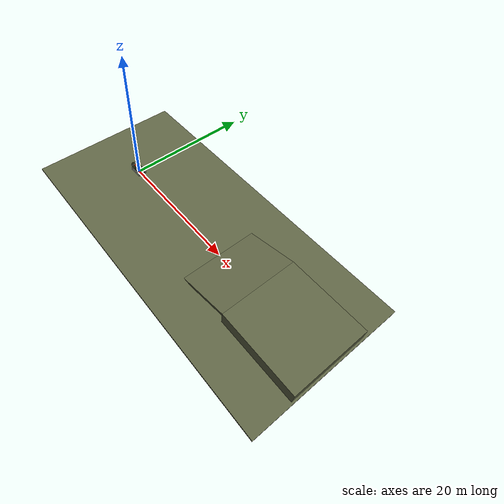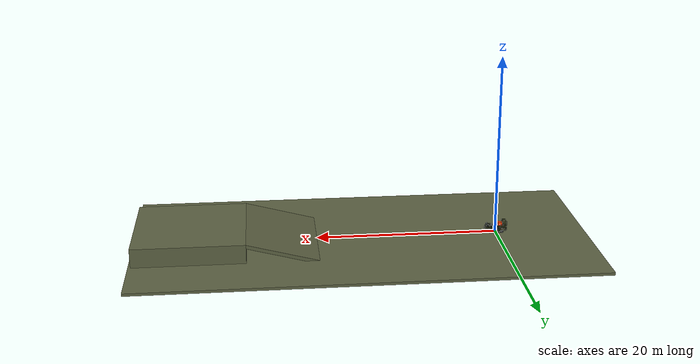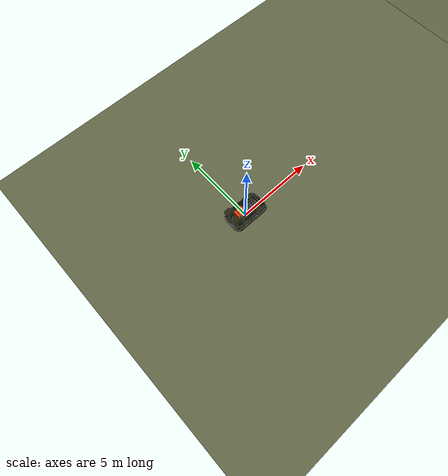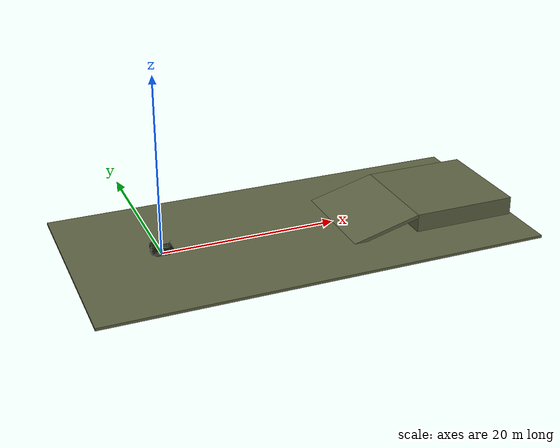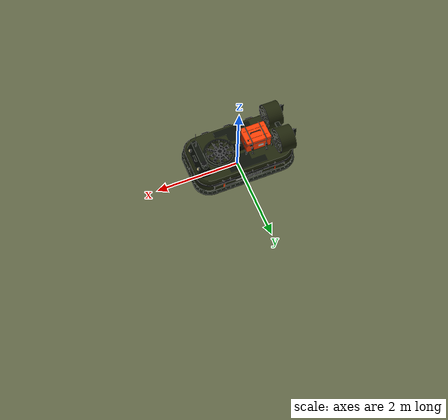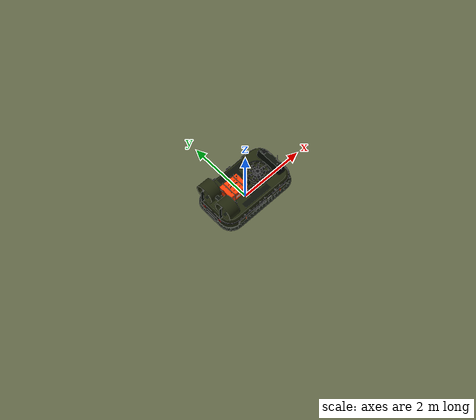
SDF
<?xml version="1.0"?>
<!-- GENERATED by hover_gazebo/scripts/gen_test_worlds_v2.py -->
<sdf version="1.9">
  <world name="v2_track_test">
    <physics name="1ms" type="dart">
      <max_step_size>0.001</max_step_size>
      <real_time_factor>1.0</real_time_factor>
      <dart><collision_detector>bullet</collision_detector></dart>
    </physics>
    <gravity>0 0 -9.81</gravity>
    <spherical_coordinates>
      <surface_model>EARTH_WGS84</surface_model>
      <latitude_deg>1.4466</latitude_deg><longitude_deg>103.7300</longitude_deg>
      <elevation>0</elevation><heading_deg>0</heading_deg>
    </spherical_coordinates>

    <plugin filename="gz-sim-physics-system" name="gz::sim::systems::Physics"/>
    <plugin filename="gz-sim-user-commands-system" name="gz::sim::systems::UserCommands"/>
    <plugin filename="gz-sim-scene-broadcaster-system" name="gz::sim::systems::SceneBroadcaster"/>
    <plugin filename="gz-sim-imu-system" name="gz::sim::systems::Imu"/>
    <plugin filename="gz-sim-navsat-system" name="gz::sim::systems::NavSat"/>
    <plugin filename="gz-sim-sensors-system" name="gz::sim::systems::Sensors">
      <render_engine>ogre2</render_engine>
    </plugin>
    <plugin filename="tidal_vehicle_plugins" name="hover::TerrainZones">
      <ground_height>0.0</ground_height>
    </plugin>
    <plugin filename="tidal_vehicle_plugins" name="hover::ScriptedCommands">
      <command><time>2.0</time><topic>/model/hovercraft_v2/cmd_vel</topic><type>gz.msgs.Twist</type><data>linear { x: 1.0 } angular { z: 0.0 }</data></command>
      <command><time>2.2</time><topic>/model/hovercraft_v2/cmd_vel</topic><type>gz.msgs.Twist</type><data>linear { x: 1.0 } angular { z: 0.0 }</data></command>
      <command><time>2.4</time><topic>/model/hovercraft_v2/cmd_vel</topic><type>gz.msgs.Twist</type><data>linear { x: 1.0 } angular { z: 0.0 }</data></command>
      <command><time>2.6</time><topic>/model/hovercraft_v2/cmd_vel</topic><type>gz.msgs.Twist</type><data>linear { x: 1.0 } angular { z: 0.0 }</data></command>
      <command><time>2.8</time><topic>/model/hovercraft_v2/cmd_vel</topic><type>gz.msgs.Twist</type><data>linear { x: 1.0 } angular { z: 0.0 }</data></command>
      <command><time>3.0</time><topic>/model/hovercraft_v2/cmd_vel</topic><type>gz.msgs.Twist</type><data>linear { x: 1.0 } angular { z: 0.0 }</data></command>
      <command><time>3.2</time><topic>/model/hovercraft_v2/cmd_vel</topic><type>gz.msgs.Twist</type><data>linear { x: 1.0 } angular { z: 0.0 }</data></command>
      <command><time>3.4</time><topic>/model/hovercraft_v2/cmd_vel</topic><type>gz.msgs.Twist</type><data>linear { x: 1.0 } angular { z: 0.0 }</data></command>
      <command><time>3.6</time><topic>/model/hovercraft_v2/cmd_vel</topic><type>gz.msgs.Twist</type><data>linear { x: 1.0 } angular { z: 0.0 }</data></command>
      <command><time>3.8</time><topic>/model/hovercraft_v2/cmd_vel</topic><type>gz.msgs.Twist</type><data>linear { x: 1.0 } angular { z: 0.0 }</data></command>
      <command><time>4.0</time><topic>/model/hovercraft_v2/cmd_vel</topic><type>gz.msgs.Twist</type><data>linear { x: 1.0 } angular { z: 0.0 }</data></command>
      <command><time>4.2</time><topic>/model/hovercraft_v2/cmd_vel</topic><type>gz.msgs.Twist</type><data>linear { x: 1.0 } angular { z: 0.0 }</data></command>
      <command><time>4.4</time><topic>/model/hovercraft_v2/cmd_vel</topic><type>gz.msgs.Twist</type><data>linear { x: 1.0 } angular { z: 0.0 }</data></command>
      <command><time>4.6</time><topic>/model/hovercraft_v2/cmd_vel</topic><type>gz.msgs.Twist</type><data>linear { x: 1.0 } angular { z: 0.0 }</data></command>
      <command><time>4.8</time><topic>/model/hovercraft_v2/cmd_vel</topic><type>gz.msgs.Twist</type><data>linear { x: 1.0 } angular { z: 0.0 }</data></command>
      <command><time>5.0</time><topic>/model/hovercraft_v2/cmd_vel</topic><type>gz.msgs.Twist</type><data>linear { x: 1.0 } angular { z: 0.0 }</data></command>
      <command><time>5.2</time><topic>/model/hovercraft_v2/cmd_vel</topic><type>gz.msgs.Twist</type><data>linear { x: 1.0 } angular { z: 0.0 }</data></command>
      <command><time>5.4</time><topic>/model/hovercraft_v2/cmd_vel</topic><type>gz.msgs.Twist</type><data>linear { x: 1.0 } angular { z: 0.0 }</data></command>
      <command><time>5.6</time><topic>/model/hovercraft_v2/cmd_vel</topic><type>gz.msgs.Twist</type><data>linear { x: 1.0 } angular { z: 0.0 }</data></command>
      <command><time>5.8</time><topic>/model/hovercraft_v2/cmd_vel</topic><type>gz.msgs.Twist</type><data>linear { x: 1.0 } angular { z: 0.0 }</data></command>
      <command><time>6.0</time><topic>/model/hovercraft_v2/cmd_vel</topic><type>gz.msgs.Twist</type><data>linear { x: 1.0 } angular { z: 0.0 }</data></command>
      <command><time>6.2</time><topic>/model/hovercraft_v2/cmd_vel</topic><type>gz.msgs.Twist</type><data>linear { x: 1.0 } angular { z: 0.0 }</data></command>
      <command><time>6.4</time><topic>/model/hovercraft_v2/cmd_vel</topic><type>gz.msgs.Twist</type><data>linear { x: 1.0 } angular { z: 0.0 }</data></command>
      <command><time>6.6</time><topic>/model/hovercraft_v2/cmd_vel</topic><type>gz.msgs.Twist</type><data>linear { x: 1.0 } angular { z: 0.0 }</data></command>
      <command><time>6.8</time><topic>/model/hovercraft_v2/cmd_vel</topic><type>gz.msgs.Twist</type><data>linear { x: 1.0 } angular { z: 0.0 }</data></command>
      <command><time>7.0</time><topic>/model/hovercraft_v2/cmd_vel</topic><type>gz.msgs.Twist</type><data>linear { x: 1.0 } angular { z: 0.0 }</data></command>
      <command><time>7.2</time><topic>/model/hovercraft_v2/cmd_vel</topic><type>gz.msgs.Twist</type><data>linear { x: 1.0 } angular { z: 0.0 }</data></command>
      <command><time>7.4</time><topic>/model/hovercraft_v2/cmd_vel</topic><type>gz.msgs.Twist</type><data>linear { x: 1.0 } angular { z: 0.0 }</data></command>
      <command><time>7.6</time><topic>/model/hovercraft_v2/cmd_vel</topic><type>gz.msgs.Twist</type><data>linear { x: 1.0 } angular { z: 0.0 }</data></command>
      <command><time>7.8</time><topic>/model/hovercraft_v2/cmd_vel</topic><type>gz.msgs.Twist</type><data>linear { x: 1.0 } angular { z: 0.0 }</data></command>
      <command><time>8.0</time><topic>/model/hovercraft_v2/cmd_vel</topic><type>gz.msgs.Twist</type><data>linear { x: 0.0 } angular { z: 0.5 }</data></command>
      <command><time>8.2</time><topic>/model/hovercraft_v2/cmd_vel</topic><type>gz.msgs.Twist</type><data>linear { x: 0.0 } angular { z: 0.5 }</data></command>
      <command><time>8.4</time><topic>/model/hovercraft_v2/cmd_vel</topic><type>gz.msgs.Twist</type><data>linear { x: 0.0 } angular { z: 0.5 }</data></command>
      <command><time>8.6</time><topic>/model/hovercraft_v2/cmd_vel</topic><type>gz.msgs.Twist</type><data>linear { x: 0.0 } angular { z: 0.5 }</data></command>
      <command><time>8.8</time><topic>/model/hovercraft_v2/cmd_vel</topic><type>gz.msgs.Twist</type><data>linear { x: 0.0 } angular { z: 0.5 }</data></command>
      <command><time>9.0</time><topic>/model/hovercraft_v2/cmd_vel</topic><type>gz.msgs.Twist</type><data>linear { x: 0.0 } angular { z: 0.5 }</data></command>
      <command><time>9.2</time><topic>/model/hovercraft_v2/cmd_vel</topic><type>gz.msgs.Twist</type><data>linear { x: 0.0 } angular { z: 0.5 }</data></command>
      <command><time>9.4</time><topic>/model/hovercraft_v2/cmd_vel</topic><type>gz.msgs.Twist</type><data>linear { x: 0.0 } angular { z: 0.5 }</data></command>
      <command><time>9.6</time><topic>/model/hovercraft_v2/cmd_vel</topic><type>gz.msgs.Twist</type><data>linear { x: 0.0 } angular { z: 0.5 }</data></command>
      <command><time>9.8</time><topic>/model/hovercraft_v2/cmd_vel</topic><type>gz.msgs.Twist</type><data>linear { x: 0.0 } angular { z: 0.5 }</data></command>
      <command><time>10.0</time><topic>/model/hovercraft_v2/cmd_vel</topic><type>gz.msgs.Twist</type><data>linear { x: 0.0 } angular { z: 0.5 }</data></command>
      <command><time>10.2</time><topic>/model/hovercraft_v2/cmd_vel</topic><type>gz.msgs.Twist</type><data>linear { x: 0.0 } angular { z: 0.5 }</data></command>
      <command><time>10.4</time><topic>/model/hovercraft_v2/cmd_vel</topic><type>gz.msgs.Twist</type><data>linear { x: 0.0 } angular { z: 0.5 }</data></command>
      <command><time>10.6</time><topic>/model/hovercraft_v2/cmd_vel</topic><type>gz.msgs.Twist</type><data>linear { x: 0.0 } angular { z: 0.5 }</data></command>
      <command><time>10.8</time><topic>/model/hovercraft_v2/cmd_vel</topic><type>gz.msgs.Twist</type><data>linear { x: 0.0 } angular { z: 0.5 }</data></command>
      <command><time>11.0</time><topic>/model/hovercraft_v2/cmd_vel</topic><type>gz.msgs.Twist</type><data>linear { x: 0.0 } angular { z: 0.5 }</data></command>
      <command><time>11.2</time><topic>/model/hovercraft_v2/cmd_vel</topic><type>gz.msgs.Twist</type><data>linear { x: 0.0 } angular { z: 0.5 }</data></command>
      <command><time>11.4</time><topic>/model/hovercraft_v2/cmd_vel</topic><type>gz.msgs.Twist</type><data>linear { x: 0.0 } angular { z: 0.5 }</data></command>
      <command><time>11.6</time><topic>/model/hovercraft_v2/cmd_vel</topic><type>gz.msgs.Twist</type><data>linear { x: 0.0 } angular { z: 0.5 }</data></command>
      <command><time>11.8</time><topic>/model/hovercraft_v2/cmd_vel</topic><type>gz.msgs.Twist</type><data>linear { x: 0.0 } angular { z: 0.5 }</data></command>
      <command><time>12.0</time><topic>/model/hovercraft_v2/cmd_vel</topic><type>gz.msgs.Twist</type><data>linear { x: 0.0 } angular { z: 0.5 }</data></command>
      <command><time>12.2</time><topic>/model/hovercraft_v2/cmd_vel</topic><type>gz.msgs.Twist</type><data>linear { x: 0.0 } angular { z: 0.5 }</data></command>
      <command><time>12.4</time><topic>/model/hovercraft_v2/cmd_vel</topic><type>gz.msgs.Twist</type><data>linear { x: 0.0 } angular { z: 0.5 }</data></command>
      <command><time>12.6</time><topic>/model/hovercraft_v2/cmd_vel</topic><type>gz.msgs.Twist</type><data>linear { x: 0.0 } angular { z: 0.5 }</data></command>
      <command><time>12.8</time><topic>/model/hovercraft_v2/cmd_vel</topic><type>gz.msgs.Twist</type><data>linear { x: 0.0 } angular { z: 0.5 }</data></command>
      <command><time>13.0</time><topic>/model/hovercraft_v2/cmd_vel</topic><type>gz.msgs.Twist</type><data>linear { x: 0.0 } angular { z: 0.5 }</data></command>
      <command><time>13.2</time><topic>/model/hovercraft_v2/cmd_vel</topic><type>gz.msgs.Twist</type><data>linear { x: 0.0 } angular { z: 0.5 }</data></command>
      <command><time>13.4</time><topic>/model/hovercraft_v2/cmd_vel</topic><type>gz.msgs.Twist</type><data>linear { x: 0.0 } angular { z: 0.5 }</data></command>
      <command><time>13.6</time><topic>/model/hovercraft_v2/cmd_vel</topic><type>gz.msgs.Twist</type><data>linear { x: 0.0 } angular { z: 0.5 }</data></command>
      <command><time>13.8</time><topic>/model/hovercraft_v2/cmd_vel</topic><type>gz.msgs.Twist</type><data>linear { x: 0.0 } angular { z: 0.5 }</data></command>
      <command><time>14.0</time><topic>/model/hovercraft_v2/cmd_vel</topic><type>gz.msgs.Twist</type><data>linear { x: 0.0 } angular { z: -0.5 }</data></command>
      <command><time>14.2</time><topic>/model/hovercraft_v2/cmd_vel</topic><type>gz.msgs.Twist</type><data>linear { x: 0.0 } angular { z: -0.5 }</data></command>
      <command><time>14.4</time><topic>/model/hovercraft_v2/cmd_vel</topic><type>gz.msgs.Twist</type><data>linear { x: 0.0 } angular { z: -0.5 }</data></command>
      <command><time>14.6</time><topic>/model/hovercraft_v2/cmd_vel</topic><type>gz.msgs.Twist</type><data>linear { x: 0.0 } angular { z: -0.5 }</data></command>
      <command><time>14.8</time><topic>/model/hovercraft_v2/cmd_vel</topic><type>gz.msgs.Twist</type><data>linear { x: 0.0 } angular { z: -0.5 }</data></command>
      <command><time>15.0</time><topic>/model/hovercraft_v2/cmd_vel</topic><type>gz.msgs.Twist</type><data>linear { x: 0.0 } angular { z: -0.5 }</data></command>
      <command><time>15.2</time><topic>/model/hovercraft_v2/cmd_vel</topic><type>gz.msgs.Twist</type><data>linear { x: 0.0 } angular { z: -0.5 }</data></command>
      <command><time>15.4</time><topic>/model/hovercraft_v2/cmd_vel</topic><type>gz.msgs.Twist</type><data>linear { x: 0.0 } angular { z: -0.5 }</data></command>
      <command><time>15.6</time><topic>/model/hovercraft_v2/cmd_vel</topic><type>gz.msgs.Twist</type><data>linear { x: 0.0 } angular { z: -0.5 }</data></command>
      <command><time>15.8</time><topic>/model/hovercraft_v2/cmd_vel</topic><type>gz.msgs.Twist</type><data>linear { x: 0.0 } angular { z: -0.5 }</data></command>
      <command><time>16.0</time><topic>/model/hovercraft_v2/cmd_vel</topic><type>gz.msgs.Twist</type><data>linear { x: 0.0 } angular { z: -0.5 }</data></command>
      <command><time>16.2</time><topic>/model/hovercraft_v2/cmd_vel</topic><type>gz.msgs.Twist</type><data>linear { x: 0.0 } angular { z: -0.5 }</data></command>
      <command><time>16.4</time><topic>/model/hovercraft_v2/cmd_vel</topic><type>gz.msgs.Twist</type><data>linear { x: 0.0 } angular { z: -0.5 }</data></command>
      <command><time>16.6</time><topic>/model/hovercraft_v2/cmd_vel</topic><type>gz.msgs.Twist</type><data>linear { x: 0.0 } angular { z: -0.5 }</data></command>
      <command><time>16.8</time><topic>/model/hovercraft_v2/cmd_vel</topic><type>gz.msgs.Twist</type><data>linear { x: 0.0 } angular { z: -0.5 }</data></command>
      <command><time>17.0</time><topic>/model/hovercraft_v2/cmd_vel</topic><type>gz.msgs.Twist</type><data>linear { x: 0.0 } angular { z: -0.5 }</data></command>
      <command><time>17.2</time><topic>/model/hovercraft_v2/cmd_vel</topic><type>gz.msgs.Twist</type><data>linear { x: 0.0 } angular { z: -0.5 }</data></command>
      <command><time>17.4</time><topic>/model/hovercraft_v2/cmd_vel</topic><type>gz.msgs.Twist</type><data>linear { x: 0.0 } angular { z: -0.5 }</data></command>
      <command><time>17.6</time><topic>/model/hovercraft_v2/cmd_vel</topic><type>gz.msgs.Twist</type><data>linear { x: 0.0 } angular { z: -0.5 }</data></command>
      <command><time>17.8</time><topic>/model/hovercraft_v2/cmd_vel</topic><type>gz.msgs.Twist</type><data>linear { x: 0.0 } angular { z: -0.5 }</data></command>
      <command><time>18.0</time><topic>/model/hovercraft_v2/cmd_vel</topic><type>gz.msgs.Twist</type><data>linear { x: 0.0 } angular { z: -0.5 }</data></command>
      <command><time>18.2</time><topic>/model/hovercraft_v2/cmd_vel</topic><type>gz.msgs.Twist</type><data>linear { x: 0.0 } angular { z: -0.5 }</data></command>
      <command><time>18.4</time><topic>/model/hovercraft_v2/cmd_vel</topic><type>gz.msgs.Twist</type><data>linear { x: 0.0 } angular { z: -0.5 }</data></command>
      <command><time>18.6</time><topic>/model/hovercraft_v2/cmd_vel</topic><type>gz.msgs.Twist</type><data>linear { x: 0.0 } angular { z: -0.5 }</data></command>
      <command><time>18.8</time><topic>/model/hovercraft_v2/cmd_vel</topic><type>gz.msgs.Twist</type><data>linear { x: 0.0 } angular { z: -0.5 }</data></command>
      <command><time>19.0</time><topic>/model/hovercraft_v2/cmd_vel</topic><type>gz.msgs.Twist</type><data>linear { x: 0.0 } angular { z: -0.5 }</data></command>
      <command><time>19.2</time><topic>/model/hovercraft_v2/cmd_vel</topic><type>gz.msgs.Twist</type><data>linear { x: 0.0 } angular { z: -0.5 }</data></command>
      <command><time>19.4</time><topic>/model/hovercraft_v2/cmd_vel</topic><type>gz.msgs.Twist</type><data>linear { x: 0.0 } angular { z: -0.5 }</data></command>
      <command><time>19.6</time><topic>/model/hovercraft_v2/cmd_vel</topic><type>gz.msgs.Twist</type><data>linear { x: 0.0 } angular { z: -0.5 }</data></command>
      <command><time>19.8</time><topic>/model/hovercraft_v2/cmd_vel</topic><type>gz.msgs.Twist</type><data>linear { x: 0.0 } angular { z: -0.5 }</data></command>
      <command><time>20.0</time><topic>/model/hovercraft_v2/cmd_vel</topic><type>gz.msgs.Twist</type><data>linear { x: 1.0 } angular { z: 0.0 }</data></command>
      <command><time>20.2</time><topic>/model/hovercraft_v2/cmd_vel</topic><type>gz.msgs.Twist</type><data>linear { x: 1.0 } angular { z: 0.0 }</data></command>
      <command><time>20.4</time><topic>/model/hovercraft_v2/cmd_vel</topic><type>gz.msgs.Twist</type><data>linear { x: 1.0 } angular { z: 0.0 }</data></command>
      <command><time>20.6</time><topic>/model/hovercraft_v2/cmd_vel</topic><type>gz.msgs.Twist</type><data>linear { x: 1.0 } angular { z: 0.0 }</data></command>
      <command><time>20.8</time><topic>/model/hovercraft_v2/cmd_vel</topic><type>gz.msgs.Twist</type><data>linear { x: 1.0 } angular { z: 0.0 }</data></command>
      <command><time>21.0</time><topic>/model/hovercraft_v2/cmd_vel</topic><type>gz.msgs.Twist</type><data>linear { x: 1.0 } angular { z: 0.0 }</data></command>
      <command><time>21.2</time><topic>/model/hovercraft_v2/cmd_vel</topic><type>gz.msgs.Twist</type><data>linear { x: 1.0 } angular { z: 0.0 }</data></command>
      <command><time>21.4</time><topic>/model/hovercraft_v2/cmd_vel</topic><type>gz.msgs.Twist</type><data>linear { x: 1.0 } angular { z: 0.0 }</data></command>
      <command><time>21.6</time><topic>/model/hovercraft_v2/cmd_vel</topic><type>gz.msgs.Twist</type><data>linear { x: 1.0 } angular { z: 0.0 }</data></command>
      <command><time>21.8</time><topic>/model/hovercraft_v2/cmd_vel</topic><type>gz.msgs.Twist</type><data>linear { x: 1.0 } angular { z: 0.0 }</data></command>
      <command><time>22.0</time><topic>/model/hovercraft_v2/cmd_vel</topic><type>gz.msgs.Twist</type><data>linear { x: 1.0 } angular { z: 0.0 }</data></command>
      <command><time>22.2</time><topic>/model/hovercraft_v2/cmd_vel</topic><type>gz.msgs.Twist</type><data>linear { x: 1.0 } angular { z: 0.0 }</data></command>
      <command><time>22.4</time><topic>/model/hovercraft_v2/cmd_vel</topic><type>gz.msgs.Twist</type><data>linear { x: 1.0 } angular { z: 0.0 }</data></command>
      <command><time>22.6</time><topic>/model/hovercraft_v2/cmd_vel</topic><type>gz.msgs.Twist</type><data>linear { x: 1.0 } angular { z: 0.0 }</data></command>
      <command><time>22.8</time><topic>/model/hovercraft_v2/cmd_vel</topic><type>gz.msgs.Twist</type><data>linear { x: 1.0 } angular { z: 0.0 }</data></command>
      <command><time>23.0</time><topic>/model/hovercraft_v2/cmd_vel</topic><type>gz.msgs.Twist</type><data>linear { x: 1.0 } angular { z: 0.0 }</data></command>
      <command><time>23.2</time><topic>/model/hovercraft_v2/cmd_vel</topic><type>gz.msgs.Twist</type><data>linear { x: 1.0 } angular { z: 0.0 }</data></command>
      <command><time>23.4</time><topic>/model/hovercraft_v2/cmd_vel</topic><type>gz.msgs.Twist</type><data>linear { x: 1.0 } angular { z: 0.0 }</data></command>
      <command><time>23.6</time><topic>/model/hovercraft_v2/cmd_vel</topic><type>gz.msgs.Twist</type><data>linear { x: 1.0 } angular { z: 0.0 }</data></command>
      <command><time>23.8</time><topic>/model/hovercraft_v2/cmd_vel</topic><type>gz.msgs.Twist</type><data>linear { x: 1.0 } angular { z: 0.0 }</data></command>
      <command><time>24.0</time><topic>/model/hovercraft_v2/cmd_vel</topic><type>gz.msgs.Twist</type><data>linear { x: 1.0 } angular { z: 0.0 }</data></command>
      <command><time>24.2</time><topic>/model/hovercraft_v2/cmd_vel</topic><type>gz.msgs.Twist</type><data>linear { x: 1.0 } angular { z: 0.0 }</data></command>
      <command><time>24.4</time><topic>/model/hovercraft_v2/cmd_vel</topic><type>gz.msgs.Twist</type><data>linear { x: 1.0 } angular { z: 0.0 }</data></command>
      <command><time>24.6</time><topic>/model/hovercraft_v2/cmd_vel</topic><type>gz.msgs.Twist</type><data>linear { x: 1.0 } angular { z: 0.0 }</data></command>
      <command><time>24.8</time><topic>/model/hovercraft_v2/cmd_vel</topic><type>gz.msgs.Twist</type><data>linear { x: 1.0 } angular { z: 0.0 }</data></command>
      <command><time>25.0</time><topic>/model/hovercraft_v2/cmd_vel</topic><type>gz.msgs.Twist</type><data>linear { x: 1.0 } angular { z: 0.0 }</data></command>
      <command><time>25.2</time><topic>/model/hovercraft_v2/cmd_vel</topic><type>gz.msgs.Twist</type><data>linear { x: 1.0 } angular { z: 0.0 }</data></command>
      <command><time>25.4</time><topic>/model/hovercraft_v2/cmd_vel</topic><type>gz.msgs.Twist</type><data>linear { x: 1.0 } angular { z: 0.0 }</data></command>
      <command><time>25.6</time><topic>/model/hovercraft_v2/cmd_vel</topic><type>gz.msgs.Twist</type><data>linear { x: 1.0 } angular { z: 0.0 }</data></command>
      <command><time>25.8</time><topic>/model/hovercraft_v2/cmd_vel</topic><type>gz.msgs.Twist</type><data>linear { x: 1.0 } angular { z: 0.0 }</data></command>
      <command><time>26.0</time><topic>/model/hovercraft_v2/cmd_vel</topic><type>gz.msgs.Twist</type><data>linear { x: 1.0 } angular { z: 0.0 }</data></command>
      <command><time>26.2</time><topic>/model/hovercraft_v2/cmd_vel</topic><type>gz.msgs.Twist</type><data>linear { x: 1.0 } angular { z: 0.0 }</data></command>
      <command><time>26.4</time><topic>/model/hovercraft_v2/cmd_vel</topic><type>gz.msgs.Twist</type><data>linear { x: 1.0 } angular { z: 0.0 }</data></command>
      <command><time>26.6</time><topic>/model/hovercraft_v2/cmd_vel</topic><type>gz.msgs.Twist</type><data>linear { x: 1.0 } angular { z: 0.0 }</data></command>
      <command><time>26.8</time><topic>/model/hovercraft_v2/cmd_vel</topic><type>gz.msgs.Twist</type><data>linear { x: 1.0 } angular { z: 0.0 }</data></command>
      <command><time>27.0</time><topic>/model/hovercraft_v2/cmd_vel</topic><type>gz.msgs.Twist</type><data>linear { x: 1.0 } angular { z: 0.0 }</data></command>
      <command><time>27.2</time><topic>/model/hovercraft_v2/cmd_vel</topic><type>gz.msgs.Twist</type><data>linear { x: 1.0 } angular { z: 0.0 }</data></command>
      <command><time>27.4</time><topic>/model/hovercraft_v2/cmd_vel</topic><type>gz.msgs.Twist</type><data>linear { x: 1.0 } angular { z: 0.0 }</data></command>
      <command><time>27.6</time><topic>/model/hovercraft_v2/cmd_vel</topic><type>gz.msgs.Twist</type><data>linear { x: 1.0 } angular { z: 0.0 }</data></command>
      <command><time>27.8</time><topic>/model/hovercraft_v2/cmd_vel</topic><type>gz.msgs.Twist</type><data>linear { x: 1.0 } angular { z: 0.0 }</data></command>
      <command><time>28.0</time><topic>/model/hovercraft_v2/cmd_vel</topic><type>gz.msgs.Twist</type><data>linear { x: 1.0 } angular { z: 0.0 }</data></command>
      <command><time>28.2</time><topic>/model/hovercraft_v2/cmd_vel</topic><type>gz.msgs.Twist</type><data>linear { x: 1.0 } angular { z: 0.0 }</data></command>
      <command><time>28.4</time><topic>/model/hovercraft_v2/cmd_vel</topic><type>gz.msgs.Twist</type><data>linear { x: 1.0 } angular { z: 0.0 }</data></command>
      <command><time>28.6</time><topic>/model/hovercraft_v2/cmd_vel</topic><type>gz.msgs.Twist</type><data>linear { x: 1.0 } angular { z: 0.0 }</data></command>
      <command><time>28.8</time><topic>/model/hovercraft_v2/cmd_vel</topic><type>gz.msgs.Twist</type><data>linear { x: 1.0 } angular { z: 0.0 }</data></command>
      <command><time>29.0</time><topic>/model/hovercraft_v2/cmd_vel</topic><type>gz.msgs.Twist</type><data>linear { x: 1.0 } angular { z: 0.0 }</data></command>
      <command><time>29.2</time><topic>/model/hovercraft_v2/cmd_vel</topic><type>gz.msgs.Twist</type><data>linear { x: 1.0 } angular { z: 0.0 }</data></command>
      <command><time>29.4</time><topic>/model/hovercraft_v2/cmd_vel</topic><type>gz.msgs.Twist</type><data>linear { x: 1.0 } angular { z: 0.0 }</data></command>
      <command><time>29.6</time><topic>/model/hovercraft_v2/cmd_vel</topic><type>gz.msgs.Twist</type><data>linear { x: 1.0 } angular { z: 0.0 }</data></command>
      <command><time>29.8</time><topic>/model/hovercraft_v2/cmd_vel</topic><type>gz.msgs.Twist</type><data>linear { x: 1.0 } angular { z: 0.0 }</data></command>
      <command><time>30.0</time><topic>/model/hovercraft_v2/cmd_vel</topic><type>gz.msgs.Twist</type><data>linear { x: 1.0 } angular { z: 0.0 }</data></command>
      <command><time>30.2</time><topic>/model/hovercraft_v2/cmd_vel</topic><type>gz.msgs.Twist</type><data>linear { x: 1.0 } angular { z: 0.0 }</data></command>
      <command><time>30.4</time><topic>/model/hovercraft_v2/cmd_vel</topic><type>gz.msgs.Twist</type><data>linear { x: 1.0 } angular { z: 0.0 }</data></command>
      <command><time>30.6</time><topic>/model/hovercraft_v2/cmd_vel</topic><type>gz.msgs.Twist</type><data>linear { x: 1.0 } angular { z: 0.0 }</data></command>
      <command><time>30.8</time><topic>/model/hovercraft_v2/cmd_vel</topic><type>gz.msgs.Twist</type><data>linear { x: 1.0 } angular { z: 0.0 }</data></command>
      <command><time>31.0</time><topic>/model/hovercraft_v2/cmd_vel</topic><type>gz.msgs.Twist</type><data>linear { x: 1.0 } angular { z: 0.0 }</data></command>
      <command><time>31.2</time><topic>/model/hovercraft_v2/cmd_vel</topic><type>gz.msgs.Twist</type><data>linear { x: 1.0 } angular { z: 0.0 }</data></command>
      <command><time>31.4</time><topic>/model/hovercraft_v2/cmd_vel</topic><type>gz.msgs.Twist</type><data>linear { x: 1.0 } angular { z: 0.0 }</data></command>
      <command><time>31.6</time><topic>/model/hovercraft_v2/cmd_vel</topic><type>gz.msgs.Twist</type><data>linear { x: 1.0 } angular { z: 0.0 }</data></command>
      <command><time>31.8</time><topic>/model/hovercraft_v2/cmd_vel</topic><type>gz.msgs.Twist</type><data>linear { x: 1.0 } angular { z: 0.0 }</data></command>
      <command><time>32.0</time><topic>/model/hovercraft_v2/cmd_vel</topic><type>gz.msgs.Twist</type><data>linear { x: 1.0 } angular { z: 0.0 }</data></command>
      <command><time>32.2</time><topic>/model/hovercraft_v2/cmd_vel</topic><type>gz.msgs.Twist</type><data>linear { x: 1.0 } angular { z: 0.0 }</data></command>
      <command><time>32.4</time><topic>/model/hovercraft_v2/cmd_vel</topic><type>gz.msgs.Twist</type><data>linear { x: 1.0 } angular { z: 0.0 }</data></command>
      <command><time>32.6</time><topic>/model/hovercraft_v2/cmd_vel</topic><type>gz.msgs.Twist</type><data>linear { x: 1.0 } angular { z: 0.0 }</data></command>
      <command><time>32.8</time><topic>/model/hovercraft_v2/cmd_vel</topic><type>gz.msgs.Twist</type><data>linear { x: 1.0 } angular { z: 0.0 }</data></command>
      <command><time>33.0</time><topic>/model/hovercraft_v2/cmd_vel</topic><type>gz.msgs.Twist</type><data>linear { x: 1.0 } angular { z: 0.0 }</data></command>
      <command><time>33.2</time><topic>/model/hovercraft_v2/cmd_vel</topic><type>gz.msgs.Twist</type><data>linear { x: 1.0 } angular { z: 0.0 }</data></command>
      <command><time>33.4</time><topic>/model/hovercraft_v2/cmd_vel</topic><type>gz.msgs.Twist</type><data>linear { x: 1.0 } angular { z: 0.0 }</data></command>
      <command><time>33.6</time><topic>/model/hovercraft_v2/cmd_vel</topic><type>gz.msgs.Twist</type><data>linear { x: 1.0 } angular { z: 0.0 }</data></command>
      <command><time>33.8</time><topic>/model/hovercraft_v2/cmd_vel</topic><type>gz.msgs.Twist</type><data>linear { x: 1.0 } angular { z: 0.0 }</data></command>
      <command><time>34.0</time><topic>/model/hovercraft_v2/cmd_vel</topic><type>gz.msgs.Twist</type><data>linear { x: 1.0 } angular { z: 0.0 }</data></command>
      <command><time>34.2</time><topic>/model/hovercraft_v2/cmd_vel</topic><type>gz.msgs.Twist</type><data>linear { x: 1.0 } angular { z: 0.0 }</data></command>
      <command><time>34.4</time><topic>/model/hovercraft_v2/cmd_vel</topic><type>gz.msgs.Twist</type><data>linear { x: 1.0 } angular { z: 0.0 }</data></command>
      <command><time>34.6</time><topic>/model/hovercraft_v2/cmd_vel</topic><type>gz.msgs.Twist</type><data>linear { x: 1.0 } angular { z: 0.0 }</data></command>
      <command><time>34.8</time><topic>/model/hovercraft_v2/cmd_vel</topic><type>gz.msgs.Twist</type><data>linear { x: 1.0 } angular { z: 0.0 }</data></command>
      <command><time>35.0</time><topic>/model/hovercraft_v2/cmd_vel</topic><type>gz.msgs.Twist</type><data>linear { x: 1.0 } angular { z: 0.0 }</data></command>
      <command><time>35.2</time><topic>/model/hovercraft_v2/cmd_vel</topic><type>gz.msgs.Twist</type><data>linear { x: 1.0 } angular { z: 0.0 }</data></command>
      <command><time>35.4</time><topic>/model/hovercraft_v2/cmd_vel</topic><type>gz.msgs.Twist</type><data>linear { x: 1.0 } angular { z: 0.0 }</data></command>
      <command><time>35.6</time><topic>/model/hovercraft_v2/cmd_vel</topic><type>gz.msgs.Twist</type><data>linear { x: 1.0 } angular { z: 0.0 }</data></command>
      <command><time>35.8</time><topic>/model/hovercraft_v2/cmd_vel</topic><type>gz.msgs.Twist</type><data>linear { x: 1.0 } angular { z: 0.0 }</data></command>
      <command><time>36.0</time><topic>/model/hovercraft_v2/cmd_vel</topic><type>gz.msgs.Twist</type><data>linear { x: 1.0 } angular { z: 0.0 }</data></command>
      <command><time>36.2</time><topic>/model/hovercraft_v2/cmd_vel</topic><type>gz.msgs.Twist</type><data>linear { x: 1.0 } angular { z: 0.0 }</data></command>
      <command><time>36.4</time><topic>/model/hovercraft_v2/cmd_vel</topic><type>gz.msgs.Twist</type><data>linear { x: 1.0 } angular { z: 0.0 }</data></command>
      <command><time>36.6</time><topic>/model/hovercraft_v2/cmd_vel</topic><type>gz.msgs.Twist</type><data>linear { x: 1.0 } angular { z: 0.0 }</data></command>
      <command><time>36.8</time><topic>/model/hovercraft_v2/cmd_vel</topic><type>gz.msgs.Twist</type><data>linear { x: 1.0 } angular { z: 0.0 }</data></command>
      <command><time>37.0</time><topic>/model/hovercraft_v2/cmd_vel</topic><type>gz.msgs.Twist</type><data>linear { x: 1.0 } angular { z: 0.0 }</data></command>
      <command><time>37.2</time><topic>/model/hovercraft_v2/cmd_vel</topic><type>gz.msgs.Twist</type><data>linear { x: 1.0 } angular { z: 0.0 }</data></command>
      <command><time>37.4</time><topic>/model/hovercraft_v2/cmd_vel</topic><type>gz.msgs.Twist</type><data>linear { x: 1.0 } angular { z: 0.0 }</data></command>
      <command><time>37.6</time><topic>/model/hovercraft_v2/cmd_vel</topic><type>gz.msgs.Twist</type><data>linear { x: 1.0 } angular { z: 0.0 }</data></command>
      <command><time>37.8</time><topic>/model/hovercraft_v2/cmd_vel</topic><type>gz.msgs.Twist</type><data>linear { x: 1.0 } angular { z: 0.0 }</data></command>
      <command><time>38.0</time><topic>/model/hovercraft_v2/cmd_vel</topic><type>gz.msgs.Twist</type><data>linear { x: 1.0 } angular { z: 0.0 }</data></command>
      <command><time>38.2</time><topic>/model/hovercraft_v2/cmd_vel</topic><type>gz.msgs.Twist</type><data>linear { x: 1.0 } angular { z: 0.0 }</data></command>
      <command><time>38.4</time><topic>/model/hovercraft_v2/cmd_vel</topic><type>gz.msgs.Twist</type><data>linear { x: 1.0 } angular { z: 0.0 }</data></command>
      <command><time>38.6</time><topic>/model/hovercraft_v2/cmd_vel</topic><type>gz.msgs.Twist</type><data>linear { x: 1.0 } angular { z: 0.0 }</data></command>
      <command><time>38.8</time><topic>/model/hovercraft_v2/cmd_vel</topic><type>gz.msgs.Twist</type><data>linear { x: 1.0 } angular { z: 0.0 }</data></command>
      <command><time>39.0</time><topic>/model/hovercraft_v2/cmd_vel</topic><type>gz.msgs.Twist</type><data>linear { x: 1.0 } angular { z: 0.0 }</data></command>
      <command><time>39.2</time><topic>/model/hovercraft_v2/cmd_vel</topic><type>gz.msgs.Twist</type><data>linear { x: 1.0 } angular { z: 0.0 }</data></command>
      <command><time>39.4</time><topic>/model/hovercraft_v2/cmd_vel</topic><type>gz.msgs.Twist</type><data>linear { x: 1.0 } angular { z: 0.0 }</data></command>
      <command><time>39.6</time><topic>/model/hovercraft_v2/cmd_vel</topic><type>gz.msgs.Twist</type><data>linear { x: 1.0 } angular { z: 0.0 }</data></command>
      <command><time>39.8</time><topic>/model/hovercraft_v2/cmd_vel</topic><type>gz.msgs.Twist</type><data>linear { x: 1.0 } angular { z: 0.0 }</data></command>
      <command><time>40.0</time><topic>/model/hovercraft_v2/cmd_vel</topic><type>gz.msgs.Twist</type><data>linear { x: 1.0 } angular { z: 0.0 }</data></command>
      <command><time>40.2</time><topic>/model/hovercraft_v2/cmd_vel</topic><type>gz.msgs.Twist</type><data>linear { x: 1.0 } angular { z: 0.0 }</data></command>
      <command><time>40.4</time><topic>/model/hovercraft_v2/cmd_vel</topic><type>gz.msgs.Twist</type><data>linear { x: 1.0 } angular { z: 0.0 }</data></command>
      <command><time>40.6</time><topic>/model/hovercraft_v2/cmd_vel</topic><type>gz.msgs.Twist</type><data>linear { x: 1.0 } angular { z: 0.0 }</data></command>
      <command><time>40.8</time><topic>/model/hovercraft_v2/cmd_vel</topic><type>gz.msgs.Twist</type><data>linear { x: 1.0 } angular { z: 0.0 }</data></command>
      <command><time>41.0</time><topic>/model/hovercraft_v2/cmd_vel</topic><type>gz.msgs.Twist</type><data>linear { x: 1.0 } angular { z: 0.0 }</data></command>
      <command><time>41.2</time><topic>/model/hovercraft_v2/cmd_vel</topic><type>gz.msgs.Twist</type><data>linear { x: 1.0 } angular { z: 0.0 }</data></command>
      <command><time>41.4</time><topic>/model/hovercraft_v2/cmd_vel</topic><type>gz.msgs.Twist</type><data>linear { x: 1.0 } angular { z: 0.0 }</data></command>
      <command><time>41.6</time><topic>/model/hovercraft_v2/cmd_vel</topic><type>gz.msgs.Twist</type><data>linear { x: 1.0 } angular { z: 0.0 }</data></command>
      <command><time>41.8</time><topic>/model/hovercraft_v2/cmd_vel</topic><type>gz.msgs.Twist</type><data>linear { x: 1.0 } angular { z: 0.0 }</data></command>
      <command><time>42.0</time><topic>/model/hovercraft_v2/cmd_vel</topic><type>gz.msgs.Twist</type><data>linear { x: 1.0 } angular { z: 0.0 }</data></command>
      <command><time>42.2</time><topic>/model/hovercraft_v2/cmd_vel</topic><type>gz.msgs.Twist</type><data>linear { x: 1.0 } angular { z: 0.0 }</data></command>
      <command><time>42.4</time><topic>/model/hovercraft_v2/cmd_vel</topic><type>gz.msgs.Twist</type><data>linear { x: 1.0 } angular { z: 0.0 }</data></command>
      <command><time>42.6</time><topic>/model/hovercraft_v2/cmd_vel</topic><type>gz.msgs.Twist</type><data>linear { x: 1.0 } angular { z: 0.0 }</data></command>
      <command><time>42.8</time><topic>/model/hovercraft_v2/cmd_vel</topic><type>gz.msgs.Twist</type><data>linear { x: 1.0 } angular { z: 0.0 }</data></command>
      <command><time>43.0</time><topic>/model/hovercraft_v2/cmd_vel</topic><type>gz.msgs.Twist</type><data>linear { x: 1.0 } angular { z: 0.0 }</data></command>
      <command><time>43.2</time><topic>/model/hovercraft_v2/cmd_vel</topic><type>gz.msgs.Twist</type><data>linear { x: 1.0 } angular { z: 0.0 }</data></command>
      <command><time>43.4</time><topic>/model/hovercraft_v2/cmd_vel</topic><type>gz.msgs.Twist</type><data>linear { x: 1.0 } angular { z: 0.0 }</data></command>
      <command><time>43.6</time><topic>/model/hovercraft_v2/cmd_vel</topic><type>gz.msgs.Twist</type><data>linear { x: 1.0 } angular { z: 0.0 }</data></command>
      <command><time>43.8</time><topic>/model/hovercraft_v2/cmd_vel</topic><type>gz.msgs.Twist</type><data>linear { x: 1.0 } angular { z: 0.0 }</data></command>
      <command><time>44.0</time><topic>/model/hovercraft_v2/cmd_vel</topic><type>gz.msgs.Twist</type><data>linear { x: 0.0 } angular { z: 0.0 }</data></command>
      <command><time>44.2</time><topic>/model/hovercraft_v2/cmd_vel</topic><type>gz.msgs.Twist</type><data>linear { x: 0.0 } angular { z: 0.0 }</data></command>
      <command><time>44.4</time><topic>/model/hovercraft_v2/cmd_vel</topic><type>gz.msgs.Twist</type><data>linear { x: 0.0 } angular { z: 0.0 }</data></command>
      <command><time>44.6</time><topic>/model/hovercraft_v2/cmd_vel</topic><type>gz.msgs.Twist</type><data>linear { x: 0.0 } angular { z: 0.0 }</data></command>
      <command><time>44.8</time><topic>/model/hovercraft_v2/cmd_vel</topic><type>gz.msgs.Twist</type><data>linear { x: 0.0 } angular { z: 0.0 }</data></command>
      <command><time>45.0</time><topic>/model/hovercraft_v2/cmd_vel</topic><type>gz.msgs.Twist</type><data>linear { x: 0.0 } angular { z: 0.0 }</data></command>
      <command><time>45.2</time><topic>/model/hovercraft_v2/cmd_vel</topic><type>gz.msgs.Twist</type><data>linear { x: 0.0 } angular { z: 0.0 }</data></command>
      <command><time>45.4</time><topic>/model/hovercraft_v2/cmd_vel</topic><type>gz.msgs.Twist</type><data>linear { x: 0.0 } angular { z: 0.0 }</data></command>
      <command><time>45.6</time><topic>/model/hovercraft_v2/cmd_vel</topic><type>gz.msgs.Twist</type><data>linear { x: 0.0 } angular { z: 0.0 }</data></command>
      <command><time>45.8</time><topic>/model/hovercraft_v2/cmd_vel</topic><type>gz.msgs.Twist</type><data>linear { x: 0.0 } angular { z: 0.0 }</data></command>
      <command><time>46.0</time><topic>/model/hovercraft_v2/cmd_vel</topic><type>gz.msgs.Twist</type><data>linear { x: 0.0 } angular { z: 0.0 }</data></command>
      <command><time>46.2</time><topic>/model/hovercraft_v2/cmd_vel</topic><type>gz.msgs.Twist</type><data>linear { x: 0.0 } angular { z: 0.0 }</data></command>
      <command><time>46.4</time><topic>/model/hovercraft_v2/cmd_vel</topic><type>gz.msgs.Twist</type><data>linear { x: 0.0 } angular { z: 0.0 }</data></command>
      <command><time>46.6</time><topic>/model/hovercraft_v2/cmd_vel</topic><type>gz.msgs.Twist</type><data>linear { x: 0.0 } angular { z: 0.0 }</data></command>
      <command><time>46.8</time><topic>/model/hovercraft_v2/cmd_vel</topic><type>gz.msgs.Twist</type><data>linear { x: 0.0 } angular { z: 0.0 }</data></command>
      <command><time>47.0</time><topic>/model/hovercraft_v2/cmd_vel</topic><type>gz.msgs.Twist</type><data>linear { x: 0.0 } angular { z: 0.0 }</data></command>
      <command><time>47.2</time><topic>/model/hovercraft_v2/cmd_vel</topic><type>gz.msgs.Twist</type><data>linear { x: 0.0 } angular { z: 0.0 }</data></command>
      <command><time>47.4</time><topic>/model/hovercraft_v2/cmd_vel</topic><type>gz.msgs.Twist</type><data>linear { x: 0.0 } angular { z: 0.0 }</data></command>
      <command><time>47.6</time><topic>/model/hovercraft_v2/cmd_vel</topic><type>gz.msgs.Twist</type><data>linear { x: 0.0 } angular { z: 0.0 }</data></command>
      <command><time>47.8</time><topic>/model/hovercraft_v2/cmd_vel</topic><type>gz.msgs.Twist</type><data>linear { x: 0.0 } angular { z: 0.0 }</data></command>
    </plugin>

    <scene><ambient>0.5 0.5 0.5 1</ambient><background>0.7 0.8 0.9 1</background><grid>false</grid></scene>
    <light type="directional" name="sun">
      <cast_shadows>true</cast_shadows><pose>0 0 10 0 0 0</pose>
      <diffuse>0.9 0.9 0.85 1</diffuse><specular>0.2 0.2 0.2 1</specular>
      <direction>-0.4 0.3 -0.9</direction>
    </light>

    <model name="ground">
      <static>true</static>
      <pose>15.0 0.0 -0.15 0 0 0</pose>
      <link name="link">
        <collision name="c">
          <geometry><box><size>50 24 0.3</size></box></geometry>
          <surface><friction><ode><mu>1.0</mu><mu2>1.0</mu2></ode></friction></surface>
        </collision>
        <visual name="v">
          <geometry><box><size>50 24 0.3</size></box></geometry>
          <material><ambient>0.36 0.38 0.26 1</ambient><diffuse>0.36 0.38 0.26 1</diffuse>
            <specular>0.05 0.05 0.05 1</specular></material>
        </visual>
      </link>
    </model>
    <model name="ramp15"><static>true</static>
      <pose>23.9155 0.0 0.8421 0 -0.26180 0</pose>
      <link name="link">
        <collision name="c"><geometry><box><size>8.0 12 0.4</size></box></geometry>
          <surface><friction><ode><mu>1.0</mu><mu2>1.0</mu2></ode></friction></surface></collision>
        <visual name="v"><geometry><box><size>8.0 12 0.4</size></box></geometry>
          <material><ambient>0.36 0.38 0.26 1</ambient><diffuse>0.36 0.38 0.26 1</diffuse></material></visual>
      </link>
    </model>
    <model name="ramp15_plateau">
      <static>true</static>
      <pose>33.72740661031254 0.0 0.885276180410083 0 0 0</pose>
      <link name="link">
        <collision name="c">
          <geometry><box><size>11.999999999999996 12 2.3705523608201657</size></box></geometry>
          <surface><friction><ode><mu>1.0</mu><mu2>1.0</mu2></ode></friction></surface>
        </collision>
        <visual name="v">
          <geometry><box><size>11.999999999999996 12 2.3705523608201657</size></box></geometry>
          <material><ambient>0.36 0.38 0.26 1</ambient><diffuse>0.36 0.38 0.26 1</diffuse>
            <specular>0.05 0.05 0.05 1</specular></material>
        </visual>
      </link>
    </model>
    <include>
      <uri>model://hovercraft_v2</uri>
      <name>hovercraft_v2</name>
      <pose>0 0 0.002 0 0 0.0</pose>
    </include>
  </world>
</sdf>

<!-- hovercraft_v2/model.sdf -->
<!-- GENERATED by tidal_vehicle_description/scripts/gen_description_v2.py from link_frames.json. Do not edit by hand. -->
<!-- Vehicle Version 2. Model frame: ground plane under hull centre; vehicle standing on its deployed tracks. -->
<!-- Total mass 300.00 kg; hull CoM offset 0.200418 0 -0.08; vehicle CoM height 0.457 m (TRACK mode). -->
<sdf version="1.9">
  <model name="hovercraft_v2">
    <self_collide>false</self_collide>

    <link name="base_link">
      <pose>0 0 0.5 0 0 0</pose>
      <inertial>
        <pose>0.200418 0 -0.08 0 0 0</pose>
        <mass>145.8</mass>
        <inertia><ixx>19.44</ixx><ixy>0</ixy><ixz>0</ixz>
                 <iyy>66.2175</iyy><iyz>0</iyz><izz>81.7695</izz></inertia>
      </inertial>
      <visual name="visual">
        <geometry><mesh><uri>model://hovercraft_v2/meshes/hull.dae</uri></mesh></geometry>
      </visual>
      <collision name="collision">
        <pose>0 0 0.01 0 0 0</pose>
        <geometry><box><size>2.3 1.2 0.4</size></box></geometry>
        <surface><friction><ode><mu>0.3</mu><mu2>0.3</mu2></ode></friction></surface>
      </collision>
      <sensor name="imu" type="imu"><pose>0 0 0 0 0 0</pose><gz_frame_id>imu_link</gz_frame_id>
        <always_on>1</always_on><update_rate>50</update_rate><topic>__default__</topic>
      </sensor>
      <sensor name="navsat" type="navsat"><pose>0.93 0.25 0.48 0 0 0</pose><gz_frame_id>base_link</gz_frame_id>
        <always_on>1</always_on><update_rate>10</update_rate>
      </sensor>
      <sensor name="ranger_fl" type="gpu_lidar"><pose>1 0.5 -0.2 0 1.5708 0</pose><gz_frame_id>base_link</gz_frame_id>
        <always_on>0</always_on><update_rate>10</update_rate>
        <!-- 5 rays over +/-3 deg (a narrow ToF beam). A single-sample gpu_lidar
             returns wrong ranges in gz-sensors 8, so don't use samples = 1. -->
        <lidar><scan><horizontal><samples>5</samples><resolution>1</resolution>
          <min_angle>-0.05</min_angle><max_angle>0.05</max_angle></horizontal></scan>
          <range><min>0.01</min><max>2.0</max><resolution>0.001</resolution></range></lidar>
      </sensor>
      <sensor name="ranger_fr" type="gpu_lidar"><pose>1 -0.5 -0.2 0 1.5708 0</pose><gz_frame_id>base_link</gz_frame_id>
        <always_on>0</always_on><update_rate>10</update_rate>
        <!-- 5 rays over +/-3 deg (a narrow ToF beam). A single-sample gpu_lidar
             returns wrong ranges in gz-sensors 8, so don't use samples = 1. -->
        <lidar><scan><horizontal><samples>5</samples><resolution>1</resolution>
          <min_angle>-0.05</min_angle><max_angle>0.05</max_angle></horizontal></scan>
          <range><min>0.01</min><max>2.0</max><resolution>0.001</resolution></range></lidar>
      </sensor>
      <sensor name="ranger_rl" type="gpu_lidar"><pose>-1 0.5 -0.2 0 1.5708 0</pose><gz_frame_id>base_link</gz_frame_id>
        <always_on>0</always_on><update_rate>10</update_rate>
        <!-- 5 rays over +/-3 deg (a narrow ToF beam). A single-sample gpu_lidar
             returns wrong ranges in gz-sensors 8, so don't use samples = 1. -->
        <lidar><scan><horizontal><samples>5</samples><resolution>1</resolution>
          <min_angle>-0.05</min_angle><max_angle>0.05</max_angle></horizontal></scan>
          <range><min>0.01</min><max>2.0</max><resolution>0.001</resolution></range></lidar>
      </sensor>
      <sensor name="ranger_rr" type="gpu_lidar"><pose>-1 -0.5 -0.2 0 1.5708 0</pose><gz_frame_id>base_link</gz_frame_id>
        <always_on>0</always_on><update_rate>10</update_rate>
        <!-- 5 rays over +/-3 deg (a narrow ToF beam). A single-sample gpu_lidar
             returns wrong ranges in gz-sensors 8, so don't use samples = 1. -->
        <lidar><scan><horizontal><samples>5</samples><resolution>1</resolution>
          <min_angle>-0.05</min_angle><max_angle>0.05</max_angle></horizontal></scan>
          <range><min>0.01</min><max>2.0</max><resolution>0.001</resolution></range></lidar>
      </sensor>
    </link>
    <link name="skirt">
      <pose>0 0 0.23 0 0 0</pose>
      <inertial>
        <pose>0 0 -0.03 0 0 0</pose>
        <mass>18.0</mass>
        <inertia><ixx>3.4614</ixx><ixy>0</ixy><ixz>0</ixz>
                 <iyy>9.4614</iyy><iyz>0</iyz><izz>12.75</izz></inertia>
      </inertial>
      <visual name="visual">
        <geometry><mesh><uri>model://hovercraft_v2/meshes/skirt.dae</uri></mesh></geometry>
      </visual>
      <collision name="collision">
        <pose>0 0 -0.03 0 0 0</pose>
        <geometry><box><size>2.5 1.5 0.24</size></box></geometry>
        <surface><friction><ode><mu>0.2</mu><mu2>0.2</mu2></ode></friction></surface>
      </collision>
    </link>
    <link name="lift_fan">
      <pose>0.45 0 0.74 0 0 0</pose>
      <inertial>
        <pose>0 0 0 0 0 0</pose>
        <mass>12.0</mass>
        <inertia><ixx>0.2368</ixx><ixy>0</ixy><ixz>0</ixz>
                 <iyy>0.2368</iyy><iyz>0</iyz><izz>0.4704</izz></inertia>
      </inertial>
      <visual name="visual">
        <geometry><mesh><uri>model://hovercraft_v2/meshes/lift_fan.dae</uri></mesh></geometry>
      </visual>
    </link>
    <link name="thrust_fan_left">
      <pose>-0.93 0.35 1.03 0 0 0</pose>
      <inertial>
        <pose>0 0 0 0 0 0</pose>
        <mass>10.0</mass>
        <inertia><ixx>0.3125</ixx><ixy>0</ixy><ixz>0</ixz>
                 <iyy>0.157583</iyy><iyz>0</iyz><izz>0.157583</izz></inertia>
      </inertial>
      <visual name="visual">
        <geometry><mesh><uri>model://hovercraft_v2/meshes/thrust_fan_left.dae</uri></mesh></geometry>
      </visual>
    </link>
    <link name="thrust_fan_right">
      <pose>-0.93 -0.35 1.03 0 0 0</pose>
      <inertial>
        <pose>0 0 0 0 0 0</pose>
        <mass>10.0</mass>
        <inertia><ixx>0.3125</ixx><ixy>0</ixy><ixz>0</ixz>
                 <iyy>0.157583</iyy><iyz>0</iyz><izz>0.157583</izz></inertia>
      </inertial>
      <visual name="visual">
        <geometry><mesh><uri>model://hovercraft_v2/meshes/thrust_fan_right.dae</uri></mesh></geometry>
      </visual>
    </link>
    <link name="rudder_left">
      <pose>-1.17 0.35 1.03 0 0 0</pose>
      <inertial>
        <pose>-0.038 0 0 0 0 0</pose>
        <mass>1.5</mass>
        <inertia><ixx>0.031268</ixx><ixy>0</ixy><ixz>0</ixz>
                 <iyy>0.0325</iyy><iyz>0</iyz><izz>0.001268</izz></inertia>
      </inertial>
      <visual name="visual">
        <geometry><mesh><uri>model://hovercraft_v2/meshes/rudder_left.dae</uri></mesh></geometry>
      </visual>
    </link>
    <link name="rudder_right">
      <pose>-1.17 -0.35 1.03 0 0 0</pose>
      <inertial>
        <pose>-0.038 0 0 0 0 0</pose>
        <mass>1.5</mass>
        <inertia><ixx>0.031268</ixx><ixy>0</ixy><ixz>0</ixz>
                 <iyy>0.0325</iyy><iyz>0</iyz><izz>0.001268</izz></inertia>
      </inertial>
      <visual name="visual">
        <geometry><mesh><uri>model://hovercraft_v2/meshes/rudder_right.dae</uri></mesh></geometry>
      </visual>
    </link>
    <link name="track_left">
      <pose>0 0.42 0.14 0 0 0</pose>
      <inertial>
        <pose>0 0 0 0 0 0</pose>
        <mass>34.0</mass>
        <inertia><ixx>0.444267</ixx><ixy>0</ixy><ixz>0</ixz>
                 <iyy>5.77547</iyy><iyz>0</iyz><izz>5.77547</izz></inertia>
      </inertial>
      <visual name="visual">
        <geometry><mesh><uri>model://hovercraft_v2/meshes/track_left.dae</uri></mesh></geometry>
      </visual>
      <collision name="collision">
        <pose>0 0 0 0 0 0</pose>
        <geometry><box><size>1.4 0.28 0.28</size></box></geometry>
        <surface><friction><ode><mu>1.0</mu><mu2>1.0</mu2></ode></friction></surface>
      </collision>
      <collision name="collision_1">
        <pose>0.7 0 0 1.5708 0 0</pose>
        <geometry><cylinder><radius>0.14</radius><length>0.28</length></cylinder></geometry>
        <surface><friction><ode><mu>1.0</mu><mu2>1.0</mu2></ode></friction></surface>
      </collision>
      <collision name="collision_2">
        <pose>-0.7 0 0 1.5708 0 0</pose>
        <geometry><cylinder><radius>0.14</radius><length>0.28</length></cylinder></geometry>
        <surface><friction><ode><mu>1.0</mu><mu2>1.0</mu2></ode></friction></surface>
      </collision>
    </link>
    <link name="track_right">
      <pose>0 -0.42 0.14 0 0 0</pose>
      <inertial>
        <pose>0 0 0 0 0 0</pose>
        <mass>34.0</mass>
        <inertia><ixx>0.444267</ixx><ixy>0</ixy><ixz>0</ixz>
                 <iyy>5.77547</iyy><iyz>0</iyz><izz>5.77547</izz></inertia>
      </inertial>
      <visual name="visual">
        <geometry><mesh><uri>model://hovercraft_v2/meshes/track_right.dae</uri></mesh></geometry>
      </visual>
      <collision name="collision">
        <pose>0 0 0 0 0 0</pose>
        <geometry><box><size>1.4 0.28 0.28</size></box></geometry>
        <surface><friction><ode><mu>1.0</mu><mu2>1.0</mu2></ode></friction></surface>
      </collision>
      <collision name="collision_1">
        <pose>0.7 0 0 1.5708 0 0</pose>
        <geometry><cylinder><radius>0.14</radius><length>0.28</length></cylinder></geometry>
        <surface><friction><ode><mu>1.0</mu><mu2>1.0</mu2></ode></friction></surface>
      </collision>
      <collision name="collision_2">
        <pose>-0.7 0 0 1.5708 0 0</pose>
        <geometry><cylinder><radius>0.14</radius><length>0.28</length></cylinder></geometry>
        <surface><friction><ode><mu>1.0</mu><mu2>1.0</mu2></ode></friction></surface>
      </collision>
    </link>
    <link name="puff_bow_left">
      <pose>0.74 0.7 0.51 0 0 0</pose>
      <inertial>
        <pose>0 0 0 0 0 0</pose>
        <mass>0.5</mass>
        <inertia><ixx>0.000818167</ixx><ixy>0</ixy><ixz>0</ixz>
                 <iyy>0.00363333</iyy><iyz>0</iyz><izz>0.00281817</izz></inertia>
      </inertial>
      <visual name="visual">
        <geometry><mesh><uri>model://hovercraft_v2/meshes/puff_bow_left.dae</uri></mesh></geometry>
      </visual>
    </link>
    <link name="puff_bow_right">
      <pose>0.74 -0.7 0.51 0 0 0</pose>
      <inertial>
        <pose>0 0 0 0 0 0</pose>
        <mass>0.5</mass>
        <inertia><ixx>0.000818167</ixx><ixy>0</ixy><ixz>0</ixz>
                 <iyy>0.00363333</iyy><iyz>0</iyz><izz>0.00281817</izz></inertia>
      </inertial>
      <visual name="visual">
        <geometry><mesh><uri>model://hovercraft_v2/meshes/puff_bow_right.dae</uri></mesh></geometry>
      </visual>
    </link>
    <link name="puff_stern_left">
      <pose>-0.74 0.7 0.51 0 0 0</pose>
      <inertial>
        <pose>0 0 0 0 0 0</pose>
        <mass>0.5</mass>
        <inertia><ixx>0.000818167</ixx><ixy>0</ixy><ixz>0</ixz>
                 <iyy>0.00363333</iyy><iyz>0</iyz><izz>0.00281817</izz></inertia>
      </inertial>
      <visual name="visual">
        <geometry><mesh><uri>model://hovercraft_v2/meshes/puff_stern_left.dae</uri></mesh></geometry>
      </visual>
    </link>
    <link name="puff_stern_right">
      <pose>-0.74 -0.7 0.51 0 0 0</pose>
      <inertial>
        <pose>0 0 0 0 0 0</pose>
        <mass>0.5</mass>
        <inertia><ixx>0.000818167</ixx><ixy>0</ixy><ixz>0</ixz>
                 <iyy>0.00363333</iyy><iyz>0</iyz><izz>0.00281817</izz></inertia>
      </inertial>
      <visual name="visual">
        <geometry><mesh><uri>model://hovercraft_v2/meshes/puff_stern_right.dae</uri></mesh></geometry>
      </visual>
    </link>
    <link name="payload_box">
      <pose>-0.42 0 0.74 0 0 0</pose>
      <inertial>
        <pose>0 0 0.175 0 0 0</pose>
        <mass>30.0</mass>
        <inertia><ixx>0.8125</ixx><ixy>0</ixy><ixz>0</ixz>
                 <iyy>1.20625</iyy><iyz>0</iyz><izz>1.40625</izz></inertia>
      </inertial>
      <visual name="visual">
        <geometry><mesh><uri>model://hovercraft_v2/meshes/payload_box.dae</uri></mesh></geometry>
      </visual>
      <collision name="collision">
        <pose>0 0 0.175 0 0 0</pose>
        <geometry><box><size>0.6 0.45 0.35</size></box></geometry>
        <surface><friction><ode><mu>0.5</mu><mu2>0.5</mu2></ode></friction></surface>
      </collision>
    </link>
    <link name="lidar_link">
      <pose>0 0 1.44 0 0 0</pose>
      <inertial>
        <pose>0 0 0 0 0 0</pose>
        <mass>1.0</mass>
        <inertia><ixx>0.00109147</ixx><ixy>0</ixy><ixz>0</ixz>
                 <iyy>0.00109147</iyy><iyz>0</iyz><izz>0.00132612</izz></inertia>
      </inertial>
      <visual name="visual">
        <geometry><mesh><uri>model://hovercraft_v2/meshes/lidar.dae</uri></mesh></geometry>
      </visual>
      <collision name="collision">
        <pose>0 0 0 0 0 0</pose>
        <geometry><cylinder><radius>0.0515</radius><length>0.0717</length></cylinder></geometry>
        <surface><friction><ode><mu>0.5</mu><mu2>0.5</mu2></ode></friction></surface>
      </collision>
      <sensor name="lidar_3d" type="gpu_lidar"><pose>0 0 0 0 0 0</pose><gz_frame_id>lidar_link</gz_frame_id>
        <always_on>1</always_on><update_rate>5</update_rate><visualize>0</visualize>
        <lidar>
          <scan>
            <horizontal><samples>360</samples><resolution>1</resolution>
              <min_angle>-3.14159</min_angle><max_angle>3.14159</max_angle></horizontal>
            <vertical><samples>8</samples><resolution>1</resolution>
              <min_angle>-0.26180</min_angle>
              <max_angle>0.26180</max_angle></vertical>
          </scan>
          <range><min>0.3</min><max>30.0</max><resolution>0.01</resolution></range>
          <noise><type>gaussian</type><mean>0</mean><stddev>0.01</stddev></noise>
        </lidar>
      </sensor>
    </link>
    <link name="camera_link">
      <pose>1.07 0 0.8 0 0 0</pose>
      <inertial>
        <pose>-0.055 0 0 0 0 0</pose>
        <mass>0.2</mass>
        <inertia><ixx>0.000295417</ixx><ixy>0</ixy><ixz>0</ixz>
                 <iyy>0.0001875</iyy><iyz>0</iyz><izz>0.000295417</izz></inertia>
      </inertial>
      <visual name="visual">
        <geometry><mesh><uri>model://hovercraft_v2/meshes/camera.dae</uri></mesh></geometry>
      </visual>
      <collision name="collision">
        <pose>-0.055 0 0 0 0 0</pose>
        <geometry><box><size>0.075 0.11 0.075</size></box></geometry>
        <surface><friction><ode><mu>0.5</mu><mu2>0.5</mu2></ode></friction></surface>
      </collision>
      <!-- Operator-camera profile: sufficient for scene awareness while
           avoiding a high-resolution render every simulation tick. -->
      <sensor name="front_camera" type="camera"><pose>0 0 0 0 0 0</pose><gz_frame_id>camera_link</gz_frame_id>
        <always_on>1</always_on><update_rate>5</update_rate>
        <camera><horizontal_fov>1.40</horizontal_fov>
          <image><width>320</width><height>240</height><format>R8G8B8</format></image>
          <clip><near>0.05</near><far>60</far></clip></camera>
      </sensor>
    </link>

    <joint name="skirt_joint" type="fixed">
      <parent>base_link</parent>
      <child>skirt</child>
    </joint>
    <joint name="lift_fan_joint" type="revolute">
      <parent>base_link</parent>
      <child>lift_fan</child>
      <axis>
        <xyz>0 0 1</xyz>
        <limit><lower>-1e16</lower><upper>1e16</upper><effort>20</effort></limit>
        <dynamics><damping>0.01</damping></dynamics>
      </axis>
    </joint>
    <joint name="thrust_fan_left_joint" type="revolute">
      <parent>base_link</parent>
      <child>thrust_fan_left</child>
      <axis>
        <xyz>1 0 0</xyz>
        <limit><lower>-1e16</lower><upper>1e16</upper><effort>20</effort></limit>
        <dynamics><damping>0.01</damping></dynamics>
      </axis>
    </joint>
    <joint name="thrust_fan_right_joint" type="revolute">
      <parent>base_link</parent>
      <child>thrust_fan_right</child>
      <axis>
        <xyz>1 0 0</xyz>
        <limit><lower>-1e16</lower><upper>1e16</upper><effort>20</effort></limit>
        <dynamics><damping>0.01</damping></dynamics>
      </axis>
    </joint>
    <joint name="rudder_left_joint" type="revolute">
      <parent>base_link</parent>
      <child>rudder_left</child>
      <axis>
        <xyz>0 0 1</xyz>
        <limit><lower>-0.5236</lower><upper>0.5236</upper><effort>20</effort></limit>
        <dynamics><damping>0.5</damping></dynamics>
      </axis>
    </joint>
    <joint name="rudder_right_joint" type="revolute">
      <parent>base_link</parent>
      <child>rudder_right</child>
      <axis>
        <xyz>0 0 1</xyz>
        <limit><lower>-0.5236</lower><upper>0.5236</upper><effort>20</effort></limit>
        <dynamics><damping>0.5</damping></dynamics>
      </axis>
    </joint>
    <joint name="track_left_joint" type="prismatic">
      <parent>base_link</parent>
      <child>track_left</child>
      <axis>
        <xyz>0 0 1</xyz>
        <limit><lower>-0.02</lower><upper>0.27</upper><effort>6000.0</effort></limit>
        <dynamics><damping>200.0</damping></dynamics>
      </axis>
    </joint>
    <joint name="track_right_joint" type="prismatic">
      <parent>base_link</parent>
      <child>track_right</child>
      <axis>
        <xyz>0 0 1</xyz>
        <limit><lower>-0.02</lower><upper>0.27</upper><effort>6000.0</effort></limit>
        <dynamics><damping>200.0</damping></dynamics>
      </axis>
    </joint>
    <joint name="puff_bow_left_joint" type="prismatic">
      <parent>base_link</parent>
      <child>puff_bow_left</child>
      <axis>
        <xyz>-1 0 0</xyz>
        <limit><lower>-0.02</lower><upper>0.28</upper><effort>20</effort></limit>
        <dynamics><damping>1.0</damping></dynamics>
      </axis>
    </joint>
    <joint name="puff_bow_right_joint" type="prismatic">
      <parent>base_link</parent>
      <child>puff_bow_right</child>
      <axis>
        <xyz>-1 0 0</xyz>
        <limit><lower>-0.02</lower><upper>0.28</upper><effort>20</effort></limit>
        <dynamics><damping>1.0</damping></dynamics>
      </axis>
    </joint>
    <joint name="puff_stern_left_joint" type="prismatic">
      <parent>base_link</parent>
      <child>puff_stern_left</child>
      <axis>
        <xyz>1 0 0</xyz>
        <limit><lower>-0.02</lower><upper>0.28</upper><effort>20</effort></limit>
        <dynamics><damping>1.0</damping></dynamics>
      </axis>
    </joint>
    <joint name="puff_stern_right_joint" type="prismatic">
      <parent>base_link</parent>
      <child>puff_stern_right</child>
      <axis>
        <xyz>1 0 0</xyz>
        <limit><lower>-0.02</lower><upper>0.28</upper><effort>20</effort></limit>
        <dynamics><damping>1.0</damping></dynamics>
      </axis>
    </joint>
    <joint name="payload_box_joint" type="fixed">
      <parent>base_link</parent>
      <child>payload_box</child>
    </joint>
    <joint name="lidar_joint" type="fixed">
      <parent>base_link</parent>
      <child>lidar_link</child>
    </joint>
    <joint name="camera_joint" type="fixed">
      <parent>base_link</parent>
      <child>camera_link</child>
    </joint>

    <plugin filename="tidal_vehicle_plugins" name="hover::AirCushion">
      <link_name>base_link</link_name>
      <corner>0.935 0.480 -0.470</corner><corner>0.935 -0.480 -0.470</corner><corner>-0.935 0.480 -0.470</corner><corner>-0.935 -0.480 -0.470</corner>
      <target_gap>0.05</target_gap>
      <stiffness>18000</stiffness>
      <damping>800</damping>
      <max_force_factor>2.0</max_force_factor>
      <spinup_time>2.0</spinup_time>
      <glide_linear_drag>50</glide_linear_drag>
      <glide_quadratic_drag>25</glide_quadratic_drag>
      <glide_yaw_drag>200</glide_yaw_drag>
      <glide_lateral_factor>3</glide_lateral_factor>
      <max_thrust>200</max_thrust>
      <thrust_time_constant>0.4</thrust_time_constant>
      <!-- reversible ducted fans (AGENTS.md): 80 % reverse thrust, so the vehicle
           can brake and hold station on the corridor's ~5 deg shore incline -->
      <reverse_thrust_fraction>0.8</reverse_thrust_fraction>
      <yaw_reserve_fraction>0.3</yaw_reserve_fraction>
      <thrust_point_left>-0.93 0.35 0.53</thrust_point_left>
      <thrust_point_right>-0.93 -0.35 0.53</thrust_point_right>
      <rudder_point>-1.17 0 0.53</rudder_point>
      <mud_viscous_drag>1800</mud_viscous_drag>
      <mud_rolling_resistance>0.25</mud_rolling_resistance>
      <mud_yaw_drag>1000</mud_yaw_drag>
      <water_hull_drag>720</water_hull_drag>
      <water_yaw_drag>500</water_yaw_drag>
      <vent_length>0.06</vent_length>
      <rudder_wash_coeff>0.55</rudder_wash_coeff>
      <rudder_control>true</rudder_control>
      <rudder_max_angle>0.4363</rudder_max_angle>
      <rudder_min_thrust>60</rudder_min_thrust>
      <rudder_rate>1.5</rudder_rate>
      <!-- puff ports: bow/stern side vents of cushion air, 2*Cd*p*A each -->
      <puff_port_force>37.5</puff_port_force>
      <puff_port_point>0.74 0.6974 0.01</puff_port_point>
      <puff_port_time_constant>0.15</puff_port_time_constant>
      <puff_lateral_gain>150</puff_lateral_gain>
      <puff_shutter_travel>0.26</puff_shutter_travel>
      <heading_kp>600</heading_kp><heading_kd>400</heading_kd>
      <speed_kp>480</speed_kp><speed_ki>120</speed_ki><yaw_rate_kp>400</yaw_rate_kp>
      <cmd_timeout>0.5</cmd_timeout>
      <use_raycast>true</use_raycast>
      <log_file>/tmp/hover_{model}.csv</log_file>
      <log_joint>track_left_joint</log_joint><log_joint>track_right_joint</log_joint>
      <log_joint>rudder_left_joint</log_joint><log_joint>puff_bow_right_joint</log_joint>
    </plugin>

    <plugin filename="gz-sim-track-controller-system" name="gz::sim::systems::TrackController">
      <link>track_left</link>
      <min_velocity>-1.92</min_velocity>
      <max_velocity>1.92</max_velocity>
    </plugin>
    <plugin filename="gz-sim-track-controller-system" name="gz::sim::systems::TrackController">
      <link>track_right</link>
      <min_velocity>-1.92</min_velocity>
      <max_velocity>1.92</max_velocity>
    </plugin>
    <plugin filename="gz-sim-tracked-vehicle-system" name="gz::sim::systems::TrackedVehicle">
      <left_track><link>track_left</link></left_track>
      <right_track><link>track_right</link></right_track>
      <tracks_separation>0.840</tracks_separation>
      <tracks_height>0.280</tracks_height>
      <steering_efficiency>0.5</steering_efficiency>
      <linear_velocity><min_velocity>-1.5</min_velocity><max_velocity>1.5</max_velocity>
        <min_acceleration>-1.5</min_acceleration><max_acceleration>1.0</max_acceleration></linear_velocity>
      <angular_velocity><min_velocity>-1.0</min_velocity><max_velocity>1.0</max_velocity>
        <min_acceleration>-2.0</min_acceleration><max_acceleration>2.0</max_acceleration></angular_velocity>
      <odom_topic>internal/track_odometry</odom_topic><tf_topic>internal/track_tf</tf_topic>
      <odom_publish_frequency>20</odom_publish_frequency>
    </plugin>

    <plugin filename="gz-sim-joint-position-controller-system" name="gz::sim::systems::JointPositionController">
      <joint_name>track_left_joint</joint_name>
      <sub_topic>tracks_cmd</sub_topic>
      <use_velocity_commands>true</use_velocity_commands>
      <p_gain>4.0</p_gain><i_gain>0</i_gain><d_gain>0</d_gain>
      <cmd_max>0.2</cmd_max><cmd_min>-0.2</cmd_min>
      <initial_position>0</initial_position>
    </plugin>
    <plugin filename="gz-sim-joint-position-controller-system" name="gz::sim::systems::JointPositionController">
      <joint_name>track_right_joint</joint_name>
      <sub_topic>tracks_cmd</sub_topic>
      <use_velocity_commands>true</use_velocity_commands>
      <p_gain>4.0</p_gain><i_gain>0</i_gain><d_gain>0</d_gain>
      <cmd_max>0.2</cmd_max><cmd_min>-0.2</cmd_min>
      <initial_position>0</initial_position>
    </plugin>
    <plugin filename="gz-sim-joint-position-controller-system" name="gz::sim::systems::JointPositionController">
      <joint_name>rudder_left_joint</joint_name><sub_topic>rudder_left_cmd</sub_topic>
      <p_gain>20</p_gain><d_gain>0.5</d_gain>
      <cmd_max>20</cmd_max><cmd_min>-20</cmd_min>
    </plugin>
    <plugin filename="gz-sim-joint-position-controller-system" name="gz::sim::systems::JointPositionController">
      <joint_name>rudder_right_joint</joint_name><sub_topic>rudder_right_cmd</sub_topic>
      <p_gain>20</p_gain><d_gain>0.5</d_gain>
      <cmd_max>20</cmd_max><cmd_min>-20</cmd_min>
    </plugin>
    <plugin filename="gz-sim-joint-position-controller-system" name="gz::sim::systems::JointPositionController">
      <joint_name>puff_bow_left_joint</joint_name><sub_topic>puff_bow_left_cmd</sub_topic>
      <use_velocity_commands>true</use_velocity_commands>
      <p_gain>10.0</p_gain><i_gain>0</i_gain><d_gain>0</d_gain>
      <cmd_max>1.0</cmd_max><cmd_min>-1.0</cmd_min>
      <initial_position>0</initial_position>
    </plugin>
    <plugin filename="gz-sim-joint-position-controller-system" name="gz::sim::systems::JointPositionController">
      <joint_name>puff_bow_right_joint</joint_name><sub_topic>puff_bow_right_cmd</sub_topic>
      <use_velocity_commands>true</use_velocity_commands>
      <p_gain>10.0</p_gain><i_gain>0</i_gain><d_gain>0</d_gain>
      <cmd_max>1.0</cmd_max><cmd_min>-1.0</cmd_min>
      <initial_position>0</initial_position>
    </plugin>
    <plugin filename="gz-sim-joint-position-controller-system" name="gz::sim::systems::JointPositionController">
      <joint_name>puff_stern_left_joint</joint_name><sub_topic>puff_stern_left_cmd</sub_topic>
      <use_velocity_commands>true</use_velocity_commands>
      <p_gain>10.0</p_gain><i_gain>0</i_gain><d_gain>0</d_gain>
      <cmd_max>1.0</cmd_max><cmd_min>-1.0</cmd_min>
      <initial_position>0</initial_position>
    </plugin>
    <plugin filename="gz-sim-joint-position-controller-system" name="gz::sim::systems::JointPositionController">
      <joint_name>puff_stern_right_joint</joint_name><sub_topic>puff_stern_right_cmd</sub_topic>
      <use_velocity_commands>true</use_velocity_commands>
      <p_gain>10.0</p_gain><i_gain>0</i_gain><d_gain>0</d_gain>
      <cmd_max>1.0</cmd_max><cmd_min>-1.0</cmd_min>
      <initial_position>0</initial_position>
    </plugin>
    <plugin filename="gz-sim-joint-state-publisher-system" name="gz::sim::systems::JointStatePublisher"/>

    <!-- /odom + TF (map -> base_link). Ground-truth pose, valid in every mode.
         Idealised: stated in docs. -->
    <plugin filename="gz-sim-odometry-publisher-system" name="gz::sim::systems::OdometryPublisher">
      <odom_frame>map</odom_frame>
      <robot_base_frame>base_link</robot_base_frame>
      <dimensions>3</dimensions>
      <odom_publish_frequency>50</odom_publish_frequency>
    </plugin>
  </model>
</sdf>
